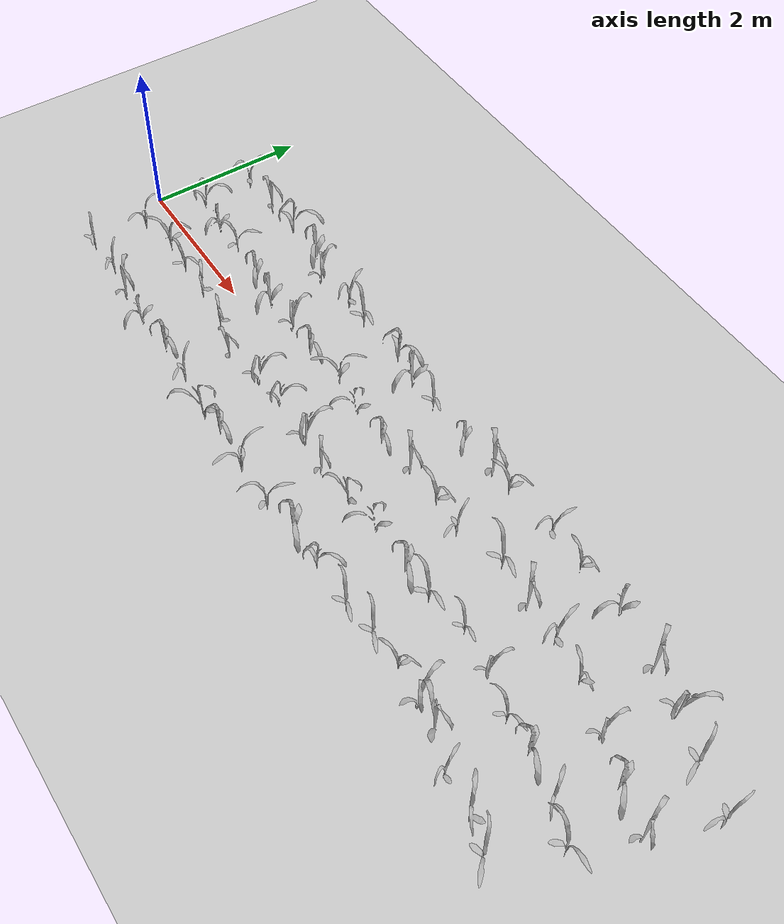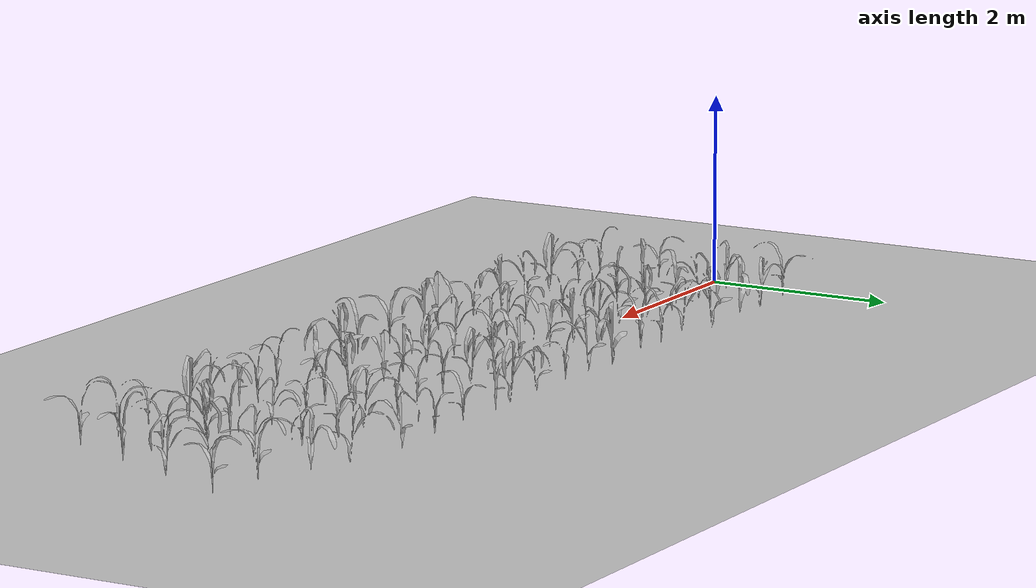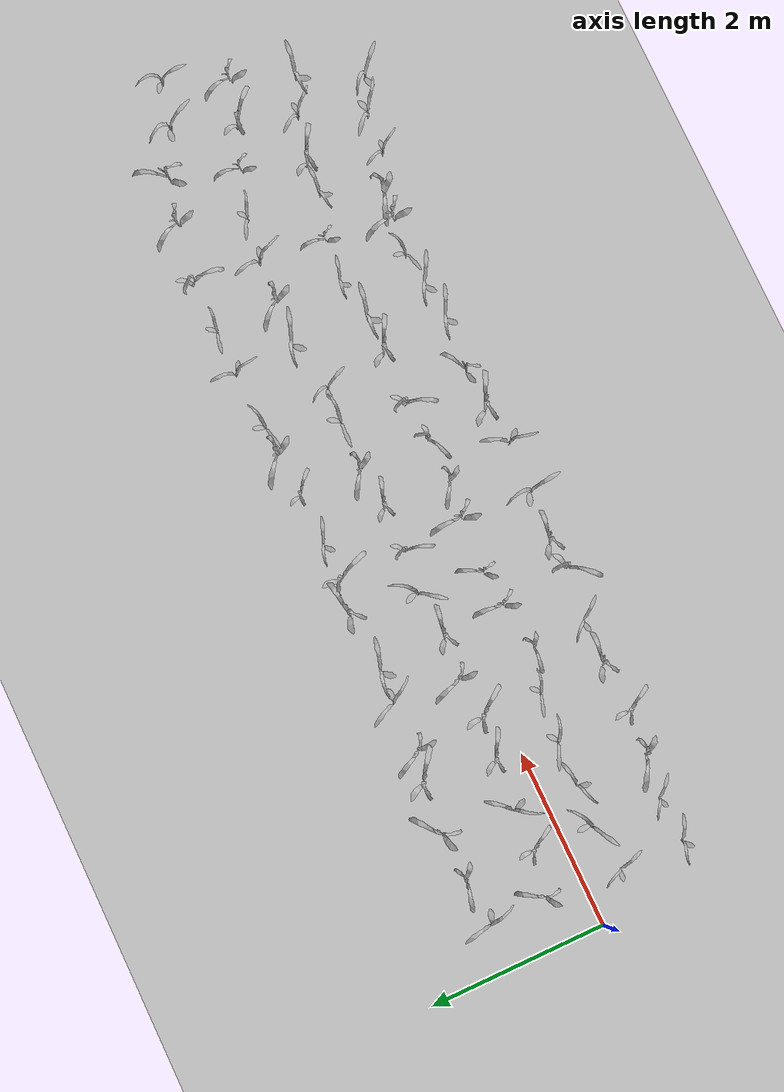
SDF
<sdf version="1.6">
 <world name="default">
  <light name="sun" type="directional">
   <pose>0 0 10 0 -0 0</pose>
   <diffuse>0.8 0.8 0.8 1</diffuse>
   <specular>0.2 0.2 0.2 1</specular>
   <attenuation>
    <range>1000</range>
    <constant>0.9</constant>
    <linear>0.01</linear>
    <quadratic>0.001</quadratic>
   </attenuation>
   <direction>-0.5 0.1 -0.9</direction>
  </light>
  <model name="ground_plane">
   <static>1</static>
   <link name="link">
    <collision name="collision">
     <geometry><plane><normal>0 0 1</normal><size>100 100</size></plane></geometry>
     <surface>
      <contact><collide_bitmask>65535</collide_bitmask></contact>
      <friction><ode><mu>100</mu><mu2>50</mu2></ode></friction>
     </surface>
    </collision>
    <visual name="visual">
     <cast_shadows>0</cast_shadows>
     <geometry><plane><normal>0 0 1</normal><size>100 100</size></plane></geometry>
     <material>
      <script><uri>file://media/materials/scripts/gazebo.material</uri><name>Gazebo/Grey</name></script>
     </material>
    </visual>
   </link>
  </model>
  <gravity>0 0 -9.8</gravity>
  <magnetic_field>6e-06 2.3e-05 -4.2e-05</magnetic_field>
  <atmosphere type="adiabatic"/>
  <physics name="default_physics" default="0" type="ode">
   <max_step_size>0.001</max_step_size>
   <real_time_factor>1</real_time_factor>
   <real_time_update_rate>1000</real_time_update_rate>
  </physics>
  <scene><ambient>0.4 0.4 0.4 1</ambient><background>0.7 0.7 0.7 1</background><shadows>1</shadows></scene>
  <audio><device>default</device></audio>
  <spherical_coordinates>
   <surface_model>EARTH_WGS84</surface_model>
   <latitude_deg>0</latitude_deg>
   <longitude_deg>0</longitude_deg>
   <elevation>0</elevation>
   <heading_deg>0</heading_deg>
  </spherical_coordinates>
  <model name="maize_01_0000">
   <pose>0.523966762746438 0.4150326742908084 0.05 0 -0 1.8050301071794776</pose>
   <link name="maize_01_0000_link">
    <inertial>
     <mass>5.0</mass>
     <inertia>
      <ixx>0.0033416667</ixx>
      <ixy>0</ixy>
      <ixz>0</ixz>
      <iyy>0.0033416667</iyy>
      <iyz>0</iyz>
      <izz>0.000016666667</izz>
     </inertia>
     <pose>0 0 0.1 0 0 0</pose>
    </inertial>
    <collision name="collision">
     <pose>0 0 0.2 0 -0 0</pose>
     <geometry><box><size>0.02 0.02 0.4</size></box></geometry>
     <surface><friction><ode><mu>10</mu><mu2>10</mu2></ode></friction></surface>
    </collision>
    <visual name="visual">
     <geometry>
      <mesh>
       <uri>model://maize_01/meshes/maize_01.dae</uri>
       <scale>0.5822569920695913 0.5822569920695913 0.5822569920695913</scale>
      </mesh>
     </geometry>
    </visual>
   </link>
  </model>
  <model name="maize_02_0001">
   <pose>0.5248532753365917 1.0798717160746447 0.05 0 -0 3.9507558975377663</pose>
   <link name="maize_02_0001_link">
    <inertial>
     <mass>5.0</mass>
     <inertia>
      <ixx>0.0033416667</ixx>
      <ixy>0</ixy>
      <ixz>0</ixz>
      <iyy>0.0033416667</iyy>
      <iyz>0</iyz>
      <izz>0.000016666667</izz>
     </inertia>
     <pose>0 0 0.1 0 0 0</pose>
    </inertial>
    <collision name="collision">
     <pose>0 0 0.2 0 -0 0</pose>
     <geometry><box><size>0.02 0.02 0.4</size></box></geometry>
     <surface><friction><ode><mu>10</mu><mu2>10</mu2></ode></friction></surface>
    </collision>
    <visual name="visual">
     <geometry>
      <mesh>
       <uri>model://maize_02/meshes/maize_02.dae</uri>
       <scale>0.6298423139953372 0.6298423139953372 0.6298423139953372</scale>
      </mesh>
     </geometry>
    </visual>
   </link>
  </model>
  <model name="maize_02_0002">
   <pose>0.46515844750414903 -0.4189155606194654 0.05 0 -0 0.9365900454225843</pose>
   <link name="maize_02_0002_link">
    <inertial>
     <mass>5.0</mass>
     <inertia>
      <ixx>0.0033416667</ixx>
      <ixy>0</ixy>
      <ixz>0</ixz>
      <iyy>0.0033416667</iyy>
      <iyz>0</iyz>
      <izz>0.000016666667</izz>
     </inertia>
     <pose>0 0 0.1 0 0 0</pose>
    </inertial>
    <collision name="collision">
     <pose>0 0 0.2 0 -0 0</pose>
     <geometry><box><size>0.02 0.02 0.4</size></box></geometry>
     <surface><friction><ode><mu>10</mu><mu2>10</mu2></ode></friction></surface>
    </collision>
    <visual name="visual">
     <geometry>
      <mesh>
       <uri>model://maize_02/meshes/maize_02.dae</uri>
       <scale>0.5298663133267577 0.5298663133267577 0.5298663133267577</scale>
      </mesh>
     </geometry>
    </visual>
   </link>
  </model>
  <model name="maize_02_0003">
   <pose>0.4602447589462634 -1.132043322837041 0.05 0 -0 1.7978640900643768</pose>
   <link name="maize_02_0003_link">
    <inertial>
     <mass>5.0</mass>
     <inertia>
      <ixx>0.0033416667</ixx>
      <ixy>0</ixy>
      <ixz>0</ixz>
      <iyy>0.0033416667</iyy>
      <iyz>0</iyz>
      <izz>0.000016666667</izz>
     </inertia>
     <pose>0 0 0.1 0 0 0</pose>
    </inertial>
    <collision name="collision">
     <pose>0 0 0.2 0 -0 0</pose>
     <geometry><box><size>0.02 0.02 0.4</size></box></geometry>
     <surface><friction><ode><mu>10</mu><mu2>10</mu2></ode></friction></surface>
    </collision>
    <visual name="visual">
     <geometry>
      <mesh>
       <uri>model://maize_02/meshes/maize_02.dae</uri>
       <scale>0.5381608076337044 0.5381608076337044 0.5381608076337044</scale>
      </mesh>
     </geometry>
    </visual>
   </link>
  </model>
  <model name="maize_01_0004">
   <pose>1.0199203152615652 0.35299629401230775 0.05 0 -0 6.0382954465742475</pose>
   <link name="maize_01_0004_link">
    <inertial>
     <mass>5.0</mass>
     <inertia>
      <ixx>0.0033416667</ixx>
      <ixy>0</ixy>
      <ixz>0</ixz>
      <iyy>0.0033416667</iyy>
      <iyz>0</iyz>
      <izz>0.000016666667</izz>
     </inertia>
     <pose>0 0 0.1 0 0 0</pose>
    </inertial>
    <collision name="collision">
     <pose>0 0 0.2 0 -0 0</pose>
     <geometry><box><size>0.02 0.02 0.4</size></box></geometry>
     <surface><friction><ode><mu>10</mu><mu2>10</mu2></ode></friction></surface>
    </collision>
    <visual name="visual">
     <geometry>
      <mesh>
       <uri>model://maize_01/meshes/maize_01.dae</uri>
       <scale>0.5396540530929095 0.5396540530929095 0.5396540530929095</scale>
      </mesh>
     </geometry>
    </visual>
   </link>
  </model>
  <model name="maize_01_0005">
   <pose>1.0654910295923556 1.105222662462426 0.05 0 -0 3.696057205758997</pose>
   <link name="maize_01_0005_link">
    <inertial>
     <mass>5.0</mass>
     <inertia>
      <ixx>0.0033416667</ixx>
      <ixy>0</ixy>
      <ixz>0</ixz>
      <iyy>0.0033416667</iyy>
      <iyz>0</iyz>
      <izz>0.000016666667</izz>
     </inertia>
     <pose>0 0 0.1 0 0 0</pose>
    </inertial>
    <collision name="collision">
     <pose>0 0 0.2 0 -0 0</pose>
     <geometry><box><size>0.02 0.02 0.4</size></box></geometry>
     <surface><friction><ode><mu>10</mu><mu2>10</mu2></ode></friction></surface>
    </collision>
    <visual name="visual">
     <geometry>
      <mesh>
       <uri>model://maize_01/meshes/maize_01.dae</uri>
       <scale>0.5877867600977696 0.5877867600977696 0.5877867600977696</scale>
      </mesh>
     </geometry>
    </visual>
   </link>
  </model>
  <model name="maize_02_0006">
   <pose>0.9898213369435384 -0.32654735532423174 0.05 0 -0 5.819287457244414</pose>
   <link name="maize_02_0006_link">
    <inertial>
     <mass>5.0</mass>
     <inertia>
      <ixx>0.0033416667</ixx>
      <ixy>0</ixy>
      <ixz>0</ixz>
      <iyy>0.0033416667</iyy>
      <iyz>0</iyz>
      <izz>0.000016666667</izz>
     </inertia>
     <pose>0 0 0.1 0 0 0</pose>
    </inertial>
    <collision name="collision">
     <pose>0 0 0.2 0 -0 0</pose>
     <geometry><box><size>0.02 0.02 0.4</size></box></geometry>
     <surface><friction><ode><mu>10</mu><mu2>10</mu2></ode></friction></surface>
    </collision>
    <visual name="visual">
     <geometry>
      <mesh>
       <uri>model://maize_02/meshes/maize_02.dae</uri>
       <scale>0.6463608204224338 0.6463608204224338 0.6463608204224338</scale>
      </mesh>
     </geometry>
    </visual>
   </link>
  </model>
  <model name="maize_02_0007">
   <pose>0.961585045974226 -1.1105220143562582 0.05 0 -0 1.4668708817369676</pose>
   <link name="maize_02_0007_link">
    <inertial>
     <mass>5.0</mass>
     <inertia>
      <ixx>0.0033416667</ixx>
      <ixy>0</ixy>
      <ixz>0</ixz>
      <iyy>0.0033416667</iyy>
      <iyz>0</iyz>
      <izz>0.000016666667</izz>
     </inertia>
     <pose>0 0 0.1 0 0 0</pose>
    </inertial>
    <collision name="collision">
     <pose>0 0 0.2 0 -0 0</pose>
     <geometry><box><size>0.02 0.02 0.4</size></box></geometry>
     <surface><friction><ode><mu>10</mu><mu2>10</mu2></ode></friction></surface>
    </collision>
    <visual name="visual">
     <geometry>
      <mesh>
       <uri>model://maize_02/meshes/maize_02.dae</uri>
       <scale>0.5000459984883049 0.5000459984883049 0.5000459984883049</scale>
      </mesh>
     </geometry>
    </visual>
   </link>
  </model>
  <model name="maize_02_0008">
   <pose>1.503632227551504 0.349260133318818 0.05 0 -0 3.076100888778547</pose>
   <link name="maize_02_0008_link">
    <inertial>
     <mass>5.0</mass>
     <inertia>
      <ixx>0.0033416667</ixx>
      <ixy>0</ixy>
      <ixz>0</ixz>
      <iyy>0.0033416667</iyy>
      <iyz>0</iyz>
      <izz>0.000016666667</izz>
     </inertia>
     <pose>0 0 0.1 0 0 0</pose>
    </inertial>
    <collision name="collision">
     <pose>0 0 0.2 0 -0 0</pose>
     <geometry><box><size>0.02 0.02 0.4</size></box></geometry>
     <surface><friction><ode><mu>10</mu><mu2>10</mu2></ode></friction></surface>
    </collision>
    <visual name="visual">
     <geometry>
      <mesh>
       <uri>model://maize_02/meshes/maize_02.dae</uri>
       <scale>0.6283412082809666 0.6283412082809666 0.6283412082809666</scale>
      </mesh>
     </geometry>
    </visual>
   </link>
  </model>
  <model name="maize_01_0009">
   <pose>1.558977972683102 1.1187317562141557 0.05 0 -0 1.4716533760433117</pose>
   <link name="maize_01_0009_link">
    <inertial>
     <mass>5.0</mass>
     <inertia>
      <ixx>0.0033416667</ixx>
      <ixy>0</ixy>
      <ixz>0</ixz>
      <iyy>0.0033416667</iyy>
      <iyz>0</iyz>
      <izz>0.000016666667</izz>
     </inertia>
     <pose>0 0 0.1 0 0 0</pose>
    </inertial>
    <collision name="collision">
     <pose>0 0 0.2 0 -0 0</pose>
     <geometry><box><size>0.02 0.02 0.4</size></box></geometry>
     <surface><friction><ode><mu>10</mu><mu2>10</mu2></ode></friction></surface>
    </collision>
    <visual name="visual">
     <geometry>
      <mesh>
       <uri>model://maize_01/meshes/maize_01.dae</uri>
       <scale>0.6826799311454922 0.6826799311454922 0.6826799311454922</scale>
      </mesh>
     </geometry>
    </visual>
   </link>
  </model>
  <model name="maize_02_0010">
   <pose>1.4536848330133545 -0.37425566543067856 0.05 0 -0 2.422375687809505</pose>
   <link name="maize_02_0010_link">
    <inertial>
     <mass>5.0</mass>
     <inertia>
      <ixx>0.0033416667</ixx>
      <ixy>0</ixy>
      <ixz>0</ixz>
      <iyy>0.0033416667</iyy>
      <iyz>0</iyz>
      <izz>0.000016666667</izz>
     </inertia>
     <pose>0 0 0.1 0 0 0</pose>
    </inertial>
    <collision name="collision">
     <pose>0 0 0.2 0 -0 0</pose>
     <geometry><box><size>0.02 0.02 0.4</size></box></geometry>
     <surface><friction><ode><mu>10</mu><mu2>10</mu2></ode></friction></surface>
    </collision>
    <visual name="visual">
     <geometry>
      <mesh>
       <uri>model://maize_02/meshes/maize_02.dae</uri>
       <scale>0.5736782465919196 0.5736782465919196 0.5736782465919196</scale>
      </mesh>
     </geometry>
    </visual>
   </link>
  </model>
  <model name="maize_01_0011">
   <pose>1.4444675356432104 -1.179642887555723 0.05 0 -0 3.4122779563719514</pose>
   <link name="maize_01_0011_link">
    <inertial>
     <mass>5.0</mass>
     <inertia>
      <ixx>0.0033416667</ixx>
      <ixy>0</ixy>
      <ixz>0</ixz>
      <iyy>0.0033416667</iyy>
      <iyz>0</iyz>
      <izz>0.000016666667</izz>
     </inertia>
     <pose>0 0 0.1 0 0 0</pose>
    </inertial>
    <collision name="collision">
     <pose>0 0 0.2 0 -0 0</pose>
     <geometry><box><size>0.02 0.02 0.4</size></box></geometry>
     <surface><friction><ode><mu>10</mu><mu2>10</mu2></ode></friction></surface>
    </collision>
    <visual name="visual">
     <geometry>
      <mesh>
       <uri>model://maize_01/meshes/maize_01.dae</uri>
       <scale>0.6784095090481377 0.6784095090481377 0.6784095090481377</scale>
      </mesh>
     </geometry>
    </visual>
   </link>
  </model>
  <model name="maize_01_0012">
   <pose>2.040732868175381 0.3005195694070919 0.05 0 -0 0.2899796782961759</pose>
   <link name="maize_01_0012_link">
    <inertial>
     <mass>5.0</mass>
     <inertia>
      <ixx>0.0033416667</ixx>
      <ixy>0</ixy>
      <ixz>0</ixz>
      <iyy>0.0033416667</iyy>
      <iyz>0</iyz>
      <izz>0.000016666667</izz>
     </inertia>
     <pose>0 0 0.1 0 0 0</pose>
    </inertial>
    <collision name="collision">
     <pose>0 0 0.2 0 -0 0</pose>
     <geometry><box><size>0.02 0.02 0.4</size></box></geometry>
     <surface><friction><ode><mu>10</mu><mu2>10</mu2></ode></friction></surface>
    </collision>
    <visual name="visual">
     <geometry>
      <mesh>
       <uri>model://maize_01/meshes/maize_01.dae</uri>
       <scale>0.595256392992198 0.595256392992198 0.595256392992198</scale>
      </mesh>
     </geometry>
    </visual>
   </link>
  </model>
  <model name="maize_01_0013">
   <pose>2.1368719891017847 1.106180763564035 0.05 0 -0 0.16974797185114474</pose>
   <link name="maize_01_0013_link">
    <inertial>
     <mass>5.0</mass>
     <inertia>
      <ixx>0.0033416667</ixx>
      <ixy>0</ixy>
      <ixz>0</ixz>
      <iyy>0.0033416667</iyy>
      <iyz>0</iyz>
      <izz>0.000016666667</izz>
     </inertia>
     <pose>0 0 0.1 0 0 0</pose>
    </inertial>
    <collision name="collision">
     <pose>0 0 0.2 0 -0 0</pose>
     <geometry><box><size>0.02 0.02 0.4</size></box></geometry>
     <surface><friction><ode><mu>10</mu><mu2>10</mu2></ode></friction></surface>
    </collision>
    <visual name="visual">
     <geometry>
      <mesh>
       <uri>model://maize_01/meshes/maize_01.dae</uri>
       <scale>0.6979724031252235 0.6979724031252235 0.6979724031252235</scale>
      </mesh>
     </geometry>
    </visual>
   </link>
  </model>
  <model name="maize_02_0014">
   <pose>1.931780257444167 -0.3824474502754521 0.05 0 -0 4.886222668759558</pose>
   <link name="maize_02_0014_link">
    <inertial>
     <mass>5.0</mass>
     <inertia>
      <ixx>0.0033416667</ixx>
      <ixy>0</ixy>
      <ixz>0</ixz>
      <iyy>0.0033416667</iyy>
      <iyz>0</iyz>
      <izz>0.000016666667</izz>
     </inertia>
     <pose>0 0 0.1 0 0 0</pose>
    </inertial>
    <collision name="collision">
     <pose>0 0 0.2 0 -0 0</pose>
     <geometry><box><size>0.02 0.02 0.4</size></box></geometry>
     <surface><friction><ode><mu>10</mu><mu2>10</mu2></ode></friction></surface>
    </collision>
    <visual name="visual">
     <geometry>
      <mesh>
       <uri>model://maize_02/meshes/maize_02.dae</uri>
       <scale>0.575836024601679 0.575836024601679 0.575836024601679</scale>
      </mesh>
     </geometry>
    </visual>
   </link>
  </model>
  <model name="maize_01_0015">
   <pose>1.9133926375941699 -1.2037670079675775 0.05 0 -0 6.033506653099774</pose>
   <link name="maize_01_0015_link">
    <inertial>
     <mass>5.0</mass>
     <inertia>
      <ixx>0.0033416667</ixx>
      <ixy>0</ixy>
      <ixz>0</ixz>
      <iyy>0.0033416667</iyy>
      <iyz>0</iyz>
      <izz>0.000016666667</izz>
     </inertia>
     <pose>0 0 0.1 0 0 0</pose>
    </inertial>
    <collision name="collision">
     <pose>0 0 0.2 0 -0 0</pose>
     <geometry><box><size>0.02 0.02 0.4</size></box></geometry>
     <surface><friction><ode><mu>10</mu><mu2>10</mu2></ode></friction></surface>
    </collision>
    <visual name="visual">
     <geometry>
      <mesh>
       <uri>model://maize_01/meshes/maize_01.dae</uri>
       <scale>0.5581267760683764 0.5581267760683764 0.5581267760683764</scale>
      </mesh>
     </geometry>
    </visual>
   </link>
  </model>
  <model name="maize_01_0016">
   <pose>2.510246999128019 0.23787252884046153 0.05 0 -0 6.144129899424734</pose>
   <link name="maize_01_0016_link">
    <inertial>
     <mass>5.0</mass>
     <inertia>
      <ixx>0.0033416667</ixx>
      <ixy>0</ixy>
      <ixz>0</ixz>
      <iyy>0.0033416667</iyy>
      <iyz>0</iyz>
      <izz>0.000016666667</izz>
     </inertia>
     <pose>0 0 0.1 0 0 0</pose>
    </inertial>
    <collision name="collision">
     <pose>0 0 0.2 0 -0 0</pose>
     <geometry><box><size>0.02 0.02 0.4</size></box></geometry>
     <surface><friction><ode><mu>10</mu><mu2>10</mu2></ode></friction></surface>
    </collision>
    <visual name="visual">
     <geometry>
      <mesh>
       <uri>model://maize_01/meshes/maize_01.dae</uri>
       <scale>0.6562338403578362 0.6562338403578362 0.6562338403578362</scale>
      </mesh>
     </geometry>
    </visual>
   </link>
  </model>
  <model name="maize_01_0017">
   <pose>2.493166982556981 0.9630720818078856 0.05 0 -0 2.861048662569731</pose>
   <link name="maize_01_0017_link">
    <inertial>
     <mass>5.0</mass>
     <inertia>
      <ixx>0.0033416667</ixx>
      <ixy>0</ixy>
      <ixz>0</ixz>
      <iyy>0.0033416667</iyy>
      <iyz>0</iyz>
      <izz>0.000016666667</izz>
     </inertia>
     <pose>0 0 0.1 0 0 0</pose>
    </inertial>
    <collision name="collision">
     <pose>0 0 0.2 0 -0 0</pose>
     <geometry><box><size>0.02 0.02 0.4</size></box></geometry>
     <surface><friction><ode><mu>10</mu><mu2>10</mu2></ode></friction></surface>
    </collision>
    <visual name="visual">
     <geometry>
      <mesh>
       <uri>model://maize_01/meshes/maize_01.dae</uri>
       <scale>0.629477505941498 0.629477505941498 0.629477505941498</scale>
      </mesh>
     </geometry>
    </visual>
   </link>
  </model>
  <model name="maize_02_0018">
   <pose>2.4838026439865604 -0.44149562420554733 0.05 0 -0 4.993970586922383</pose>
   <link name="maize_02_0018_link">
    <inertial>
     <mass>5.0</mass>
     <inertia>
      <ixx>0.0033416667</ixx>
      <ixy>0</ixy>
      <ixz>0</ixz>
      <iyy>0.0033416667</iyy>
      <iyz>0</iyz>
      <izz>0.000016666667</izz>
     </inertia>
     <pose>0 0 0.1 0 0 0</pose>
    </inertial>
    <collision name="collision">
     <pose>0 0 0.2 0 -0 0</pose>
     <geometry><box><size>0.02 0.02 0.4</size></box></geometry>
     <surface><friction><ode><mu>10</mu><mu2>10</mu2></ode></friction></surface>
    </collision>
    <visual name="visual">
     <geometry>
      <mesh>
       <uri>model://maize_02/meshes/maize_02.dae</uri>
       <scale>0.5095507926992316 0.5095507926992316 0.5095507926992316</scale>
      </mesh>
     </geometry>
    </visual>
   </link>
  </model>
  <model name="maize_01_0019">
   <pose>2.4671652501393573 -1.1738254497009892 0.05 0 -0 0.7211971315318042</pose>
   <link name="maize_01_0019_link">
    <inertial>
     <mass>5.0</mass>
     <inertia>
      <ixx>0.0033416667</ixx>
      <ixy>0</ixy>
      <ixz>0</ixz>
      <iyy>0.0033416667</iyy>
      <iyz>0</iyz>
      <izz>0.000016666667</izz>
     </inertia>
     <pose>0 0 0.1 0 0 0</pose>
    </inertial>
    <collision name="collision">
     <pose>0 0 0.2 0 -0 0</pose>
     <geometry><box><size>0.02 0.02 0.4</size></box></geometry>
     <surface><friction><ode><mu>10</mu><mu2>10</mu2></ode></friction></surface>
    </collision>
    <visual name="visual">
     <geometry>
      <mesh>
       <uri>model://maize_01/meshes/maize_01.dae</uri>
       <scale>0.629807478542989 0.629807478542989 0.629807478542989</scale>
      </mesh>
     </geometry>
    </visual>
   </link>
  </model>
  <model name="maize_01_0020">
   <pose>2.9889529004716753 0.25801577047027513 0.05 0 -0 2.71639642661828</pose>
   <link name="maize_01_0020_link">
    <inertial>
     <mass>5.0</mass>
     <inertia>
      <ixx>0.0033416667</ixx>
      <ixy>0</ixy>
      <ixz>0</ixz>
      <iyy>0.0033416667</iyy>
      <iyz>0</iyz>
      <izz>0.000016666667</izz>
     </inertia>
     <pose>0 0 0.1 0 0 0</pose>
    </inertial>
    <collision name="collision">
     <pose>0 0 0.2 0 -0 0</pose>
     <geometry><box><size>0.02 0.02 0.4</size></box></geometry>
     <surface><friction><ode><mu>10</mu><mu2>10</mu2></ode></friction></surface>
    </collision>
    <visual name="visual">
     <geometry>
      <mesh>
       <uri>model://maize_01/meshes/maize_01.dae</uri>
       <scale>0.6221070844538605 0.6221070844538605 0.6221070844538605</scale>
      </mesh>
     </geometry>
    </visual>
   </link>
  </model>
  <model name="maize_02_0021">
   <pose>3.0520632059223862 1.0240751103559858 0.05 0 -0 4.261147328329564</pose>
   <link name="maize_02_0021_link">
    <inertial>
     <mass>5.0</mass>
     <inertia>
      <ixx>0.0033416667</ixx>
      <ixy>0</ixy>
      <ixz>0</ixz>
      <iyy>0.0033416667</iyy>
      <iyz>0</iyz>
      <izz>0.000016666667</izz>
     </inertia>
     <pose>0 0 0.1 0 0 0</pose>
    </inertial>
    <collision name="collision">
     <pose>0 0 0.2 0 -0 0</pose>
     <geometry><box><size>0.02 0.02 0.4</size></box></geometry>
     <surface><friction><ode><mu>10</mu><mu2>10</mu2></ode></friction></surface>
    </collision>
    <visual name="visual">
     <geometry>
      <mesh>
       <uri>model://maize_02/meshes/maize_02.dae</uri>
       <scale>0.6331911358099501 0.6331911358099501 0.6331911358099501</scale>
      </mesh>
     </geometry>
    </visual>
   </link>
  </model>
  <model name="maize_01_0022">
   <pose>2.97400271973419 -0.5918598628877113 0.05 0 -0 3.7910285614634462</pose>
   <link name="maize_01_0022_link">
    <inertial>
     <mass>5.0</mass>
     <inertia>
      <ixx>0.0033416667</ixx>
      <ixy>0</ixy>
      <ixz>0</ixz>
      <iyy>0.0033416667</iyy>
      <iyz>0</iyz>
      <izz>0.000016666667</izz>
     </inertia>
     <pose>0 0 0.1 0 0 0</pose>
    </inertial>
    <collision name="collision">
     <pose>0 0 0.2 0 -0 0</pose>
     <geometry><box><size>0.02 0.02 0.4</size></box></geometry>
     <surface><friction><ode><mu>10</mu><mu2>10</mu2></ode></friction></surface>
    </collision>
    <visual name="visual">
     <geometry>
      <mesh>
       <uri>model://maize_01/meshes/maize_01.dae</uri>
       <scale>0.5028517858773822 0.5028517858773822 0.5028517858773822</scale>
      </mesh>
     </geometry>
    </visual>
   </link>
  </model>
  <model name="maize_02_0023">
   <pose>2.994720311939697 -1.1945998067587797 0.05 0 -0 1.3100654780904493</pose>
   <link name="maize_02_0023_link">
    <inertial>
     <mass>5.0</mass>
     <inertia>
      <ixx>0.0033416667</ixx>
      <ixy>0</ixy>
      <ixz>0</ixz>
      <iyy>0.0033416667</iyy>
      <iyz>0</iyz>
      <izz>0.000016666667</izz>
     </inertia>
     <pose>0 0 0.1 0 0 0</pose>
    </inertial>
    <collision name="collision">
     <pose>0 0 0.2 0 -0 0</pose>
     <geometry><box><size>0.02 0.02 0.4</size></box></geometry>
     <surface><friction><ode><mu>10</mu><mu2>10</mu2></ode></friction></surface>
    </collision>
    <visual name="visual">
     <geometry>
      <mesh>
       <uri>model://maize_02/meshes/maize_02.dae</uri>
       <scale>0.5348060385841131 0.5348060385841131 0.5348060385841131</scale>
      </mesh>
     </geometry>
    </visual>
   </link>
  </model>
  <model name="maize_01_0024">
   <pose>3.443074180217835 0.2284497880585611 0.05 0 -0 0.639792568922252</pose>
   <link name="maize_01_0024_link">
    <inertial>
     <mass>5.0</mass>
     <inertia>
      <ixx>0.0033416667</ixx>
      <ixy>0</ixy>
      <ixz>0</ixz>
      <iyy>0.0033416667</iyy>
      <iyz>0</iyz>
      <izz>0.000016666667</izz>
     </inertia>
     <pose>0 0 0.1 0 0 0</pose>
    </inertial>
    <collision name="collision">
     <pose>0 0 0.2 0 -0 0</pose>
     <geometry><box><size>0.02 0.02 0.4</size></box></geometry>
     <surface><friction><ode><mu>10</mu><mu2>10</mu2></ode></friction></surface>
    </collision>
    <visual name="visual">
     <geometry>
      <mesh>
       <uri>model://maize_01/meshes/maize_01.dae</uri>
       <scale>0.6128064751184193 0.6128064751184193 0.6128064751184193</scale>
      </mesh>
     </geometry>
    </visual>
   </link>
  </model>
  <model name="maize_02_0025">
   <pose>3.423280574257146 0.992229800525366 0.05 0 -0 1.9450103717449692</pose>
   <link name="maize_02_0025_link">
    <inertial>
     <mass>5.0</mass>
     <inertia>
      <ixx>0.0033416667</ixx>
      <ixy>0</ixy>
      <ixz>0</ixz>
      <iyy>0.0033416667</iyy>
      <iyz>0</iyz>
      <izz>0.000016666667</izz>
     </inertia>
     <pose>0 0 0.1 0 0 0</pose>
    </inertial>
    <collision name="collision">
     <pose>0 0 0.2 0 -0 0</pose>
     <geometry><box><size>0.02 0.02 0.4</size></box></geometry>
     <surface><friction><ode><mu>10</mu><mu2>10</mu2></ode></friction></surface>
    </collision>
    <visual name="visual">
     <geometry>
      <mesh>
       <uri>model://maize_02/meshes/maize_02.dae</uri>
       <scale>0.665604324518885 0.665604324518885 0.665604324518885</scale>
      </mesh>
     </geometry>
    </visual>
   </link>
  </model>
  <model name="maize_01_0026">
   <pose>3.5062867528112833 -0.5004778221379712 0.05 0 -0 2.3216417221331356</pose>
   <link name="maize_01_0026_link">
    <inertial>
     <mass>5.0</mass>
     <inertia>
      <ixx>0.0033416667</ixx>
      <ixy>0</ixy>
      <ixz>0</ixz>
      <iyy>0.0033416667</iyy>
      <iyz>0</iyz>
      <izz>0.000016666667</izz>
     </inertia>
     <pose>0 0 0.1 0 0 0</pose>
    </inertial>
    <collision name="collision">
     <pose>0 0 0.2 0 -0 0</pose>
     <geometry><box><size>0.02 0.02 0.4</size></box></geometry>
     <surface><friction><ode><mu>10</mu><mu2>10</mu2></ode></friction></surface>
    </collision>
    <visual name="visual">
     <geometry>
      <mesh>
       <uri>model://maize_01/meshes/maize_01.dae</uri>
       <scale>0.6098890040684718 0.6098890040684718 0.6098890040684718</scale>
      </mesh>
     </geometry>
    </visual>
   </link>
  </model>
  <model name="maize_01_0027">
   <pose>3.5920836885190277 -1.2672288973604182 0.05 0 -0 4.774702933948235</pose>
   <link name="maize_01_0027_link">
    <inertial>
     <mass>5.0</mass>
     <inertia>
      <ixx>0.0033416667</ixx>
      <ixy>0</ixy>
      <ixz>0</ixz>
      <iyy>0.0033416667</iyy>
      <iyz>0</iyz>
      <izz>0.000016666667</izz>
     </inertia>
     <pose>0 0 0.1 0 0 0</pose>
    </inertial>
    <collision name="collision">
     <pose>0 0 0.2 0 -0 0</pose>
     <geometry><box><size>0.02 0.02 0.4</size></box></geometry>
     <surface><friction><ode><mu>10</mu><mu2>10</mu2></ode></friction></surface>
    </collision>
    <visual name="visual">
     <geometry>
      <mesh>
       <uri>model://maize_01/meshes/maize_01.dae</uri>
       <scale>0.6556921403700694 0.6556921403700694 0.6556921403700694</scale>
      </mesh>
     </geometry>
    </visual>
   </link>
  </model>
  <model name="maize_02_0028">
   <pose>4.002339001380929 0.28708051347078645 0.05 0 -0 6.212871286915344</pose>
   <link name="maize_02_0028_link">
    <inertial>
     <mass>5.0</mass>
     <inertia>
      <ixx>0.0033416667</ixx>
      <ixy>0</ixy>
      <ixz>0</ixz>
      <iyy>0.0033416667</iyy>
      <iyz>0</iyz>
      <izz>0.000016666667</izz>
     </inertia>
     <pose>0 0 0.1 0 0 0</pose>
    </inertial>
    <collision name="collision">
     <pose>0 0 0.2 0 -0 0</pose>
     <geometry><box><size>0.02 0.02 0.4</size></box></geometry>
     <surface><friction><ode><mu>10</mu><mu2>10</mu2></ode></friction></surface>
    </collision>
    <visual name="visual">
     <geometry>
      <mesh>
       <uri>model://maize_02/meshes/maize_02.dae</uri>
       <scale>0.6356348580165118 0.6356348580165118 0.6356348580165118</scale>
      </mesh>
     </geometry>
    </visual>
   </link>
  </model>
  <model name="maize_01_0029">
   <pose>4.089465292540867 1.0392879885186976 0.05 0 -0 0.9478603963230247</pose>
   <link name="maize_01_0029_link">
    <inertial>
     <mass>5.0</mass>
     <inertia>
      <ixx>0.0033416667</ixx>
      <ixy>0</ixy>
      <ixz>0</ixz>
      <iyy>0.0033416667</iyy>
      <iyz>0</iyz>
      <izz>0.000016666667</izz>
     </inertia>
     <pose>0 0 0.1 0 0 0</pose>
    </inertial>
    <collision name="collision">
     <pose>0 0 0.2 0 -0 0</pose>
     <geometry><box><size>0.02 0.02 0.4</size></box></geometry>
     <surface><friction><ode><mu>10</mu><mu2>10</mu2></ode></friction></surface>
    </collision>
    <visual name="visual">
     <geometry>
      <mesh>
       <uri>model://maize_01/meshes/maize_01.dae</uri>
       <scale>0.6862345623201176 0.6862345623201176 0.6862345623201176</scale>
      </mesh>
     </geometry>
    </visual>
   </link>
  </model>
  <model name="maize_01_0030">
   <pose>3.9111913381568097 -0.46276025048916475 0.05 0 -0 1.9455105480501291</pose>
   <link name="maize_01_0030_link">
    <inertial>
     <mass>5.0</mass>
     <inertia>
      <ixx>0.0033416667</ixx>
      <ixy>0</ixy>
      <ixz>0</ixz>
      <iyy>0.0033416667</iyy>
      <iyz>0</iyz>
      <izz>0.000016666667</izz>
     </inertia>
     <pose>0 0 0.1 0 0 0</pose>
    </inertial>
    <collision name="collision">
     <pose>0 0 0.2 0 -0 0</pose>
     <geometry><box><size>0.02 0.02 0.4</size></box></geometry>
     <surface><friction><ode><mu>10</mu><mu2>10</mu2></ode></friction></surface>
    </collision>
    <visual name="visual">
     <geometry>
      <mesh>
       <uri>model://maize_01/meshes/maize_01.dae</uri>
       <scale>0.526570501130631 0.526570501130631 0.526570501130631</scale>
      </mesh>
     </geometry>
    </visual>
   </link>
  </model>
  <model name="maize_01_0031">
   <pose>3.8928818067296707 -1.2288936645430941 0.05 0 -0 0.6694644330116607</pose>
   <link name="maize_01_0031_link">
    <inertial>
     <mass>5.0</mass>
     <inertia>
      <ixx>0.0033416667</ixx>
      <ixy>0</ixy>
      <ixz>0</ixz>
      <iyy>0.0033416667</iyy>
      <iyz>0</iyz>
      <izz>0.000016666667</izz>
     </inertia>
     <pose>0 0 0.1 0 0 0</pose>
    </inertial>
    <collision name="collision">
     <pose>0 0 0.2 0 -0 0</pose>
     <geometry><box><size>0.02 0.02 0.4</size></box></geometry>
     <surface><friction><ode><mu>10</mu><mu2>10</mu2></ode></friction></surface>
    </collision>
    <visual name="visual">
     <geometry>
      <mesh>
       <uri>model://maize_01/meshes/maize_01.dae</uri>
       <scale>0.6072951427507317 0.6072951427507317 0.6072951427507317</scale>
      </mesh>
     </geometry>
    </visual>
   </link>
  </model>
  <model name="maize_01_0032">
   <pose>4.483130657835956 0.2181703435077315 0.05 0 -0 5.194716972884884</pose>
   <link name="maize_01_0032_link">
    <inertial>
     <mass>5.0</mass>
     <inertia>
      <ixx>0.0033416667</ixx>
      <ixy>0</ixy>
      <ixz>0</ixz>
      <iyy>0.0033416667</iyy>
      <iyz>0</iyz>
      <izz>0.000016666667</izz>
     </inertia>
     <pose>0 0 0.1 0 0 0</pose>
    </inertial>
    <collision name="collision">
     <pose>0 0 0.2 0 -0 0</pose>
     <geometry><box><size>0.02 0.02 0.4</size></box></geometry>
     <surface><friction><ode><mu>10</mu><mu2>10</mu2></ode></friction></surface>
    </collision>
    <visual name="visual">
     <geometry>
      <mesh>
       <uri>model://maize_01/meshes/maize_01.dae</uri>
       <scale>0.5381228093750381 0.5381228093750381 0.5381228093750381</scale>
      </mesh>
     </geometry>
    </visual>
   </link>
  </model>
  <model name="maize_01_0033">
   <pose>4.474949129762452 0.9862563068267514 0.05 0 -0 5.887725121790559</pose>
   <link name="maize_01_0033_link">
    <inertial>
     <mass>5.0</mass>
     <inertia>
      <ixx>0.0033416667</ixx>
      <ixy>0</ixy>
      <ixz>0</ixz>
      <iyy>0.0033416667</iyy>
      <iyz>0</iyz>
      <izz>0.000016666667</izz>
     </inertia>
     <pose>0 0 0.1 0 0 0</pose>
    </inertial>
    <collision name="collision">
     <pose>0 0 0.2 0 -0 0</pose>
     <geometry><box><size>0.02 0.02 0.4</size></box></geometry>
     <surface><friction><ode><mu>10</mu><mu2>10</mu2></ode></friction></surface>
    </collision>
    <visual name="visual">
     <geometry>
      <mesh>
       <uri>model://maize_01/meshes/maize_01.dae</uri>
       <scale>0.6739857275312071 0.6739857275312071 0.6739857275312071</scale>
      </mesh>
     </geometry>
    </visual>
   </link>
  </model>
  <model name="maize_01_0034">
   <pose>4.544771440879142 -0.5000676885154269 0.05 0 -0 2.4597328034436954</pose>
   <link name="maize_01_0034_link">
    <inertial>
     <mass>5.0</mass>
     <inertia>
      <ixx>0.0033416667</ixx>
      <ixy>0</ixy>
      <ixz>0</ixz>
      <iyy>0.0033416667</iyy>
      <iyz>0</iyz>
      <izz>0.000016666667</izz>
     </inertia>
     <pose>0 0 0.1 0 0 0</pose>
    </inertial>
    <collision name="collision">
     <pose>0 0 0.2 0 -0 0</pose>
     <geometry><box><size>0.02 0.02 0.4</size></box></geometry>
     <surface><friction><ode><mu>10</mu><mu2>10</mu2></ode></friction></surface>
    </collision>
    <visual name="visual">
     <geometry>
      <mesh>
       <uri>model://maize_01/meshes/maize_01.dae</uri>
       <scale>0.6755858032378665 0.6755858032378665 0.6755858032378665</scale>
      </mesh>
     </geometry>
    </visual>
   </link>
  </model>
  <model name="maize_02_0035">
   <pose>4.48810724896792 -1.282390259113714 0.05 0 -0 0.7057874232195723</pose>
   <link name="maize_02_0035_link">
    <inertial>
     <mass>5.0</mass>
     <inertia>
      <ixx>0.0033416667</ixx>
      <ixy>0</ixy>
      <ixz>0</ixz>
      <iyy>0.0033416667</iyy>
      <iyz>0</iyz>
      <izz>0.000016666667</izz>
     </inertia>
     <pose>0 0 0.1 0 0 0</pose>
    </inertial>
    <collision name="collision">
     <pose>0 0 0.2 0 -0 0</pose>
     <geometry><box><size>0.02 0.02 0.4</size></box></geometry>
     <surface><friction><ode><mu>10</mu><mu2>10</mu2></ode></friction></surface>
    </collision>
    <visual name="visual">
     <geometry>
      <mesh>
       <uri>model://maize_02/meshes/maize_02.dae</uri>
       <scale>0.6703926624739526 0.6703926624739526 0.6703926624739526</scale>
      </mesh>
     </geometry>
    </visual>
   </link>
  </model>
  <model name="maize_01_0036">
   <pose>4.991810056498151 0.2211237160717848 0.05 0 -0 0.48154976762973434</pose>
   <link name="maize_01_0036_link">
    <inertial>
     <mass>5.0</mass>
     <inertia>
      <ixx>0.0033416667</ixx>
      <ixy>0</ixy>
      <ixz>0</ixz>
      <iyy>0.0033416667</iyy>
      <iyz>0</iyz>
      <izz>0.000016666667</izz>
     </inertia>
     <pose>0 0 0.1 0 0 0</pose>
    </inertial>
    <collision name="collision">
     <pose>0 0 0.2 0 -0 0</pose>
     <geometry><box><size>0.02 0.02 0.4</size></box></geometry>
     <surface><friction><ode><mu>10</mu><mu2>10</mu2></ode></friction></surface>
    </collision>
    <visual name="visual">
     <geometry>
      <mesh>
       <uri>model://maize_01/meshes/maize_01.dae</uri>
       <scale>0.5598796415592937 0.5598796415592937 0.5598796415592937</scale>
      </mesh>
     </geometry>
    </visual>
   </link>
  </model>
  <model name="maize_02_0037">
   <pose>4.908736499374385 0.9768782011245747 0.05 0 -0 1.8294438370918091</pose>
   <link name="maize_02_0037_link">
    <inertial>
     <mass>5.0</mass>
     <inertia>
      <ixx>0.0033416667</ixx>
      <ixy>0</ixy>
      <ixz>0</ixz>
      <iyy>0.0033416667</iyy>
      <iyz>0</iyz>
      <izz>0.000016666667</izz>
     </inertia>
     <pose>0 0 0.1 0 0 0</pose>
    </inertial>
    <collision name="collision">
     <pose>0 0 0.2 0 -0 0</pose>
     <geometry><box><size>0.02 0.02 0.4</size></box></geometry>
     <surface><friction><ode><mu>10</mu><mu2>10</mu2></ode></friction></surface>
    </collision>
    <visual name="visual">
     <geometry>
      <mesh>
       <uri>model://maize_02/meshes/maize_02.dae</uri>
       <scale>0.5496664147344748 0.5496664147344748 0.5496664147344748</scale>
      </mesh>
     </geometry>
    </visual>
   </link>
  </model>
  <model name="maize_01_0038">
   <pose>4.976571551156914 -0.5525297962804545 0.05 0 -0 3.379482973106335</pose>
   <link name="maize_01_0038_link">
    <inertial>
     <mass>5.0</mass>
     <inertia>
      <ixx>0.0033416667</ixx>
      <ixy>0</ixy>
      <ixz>0</ixz>
      <iyy>0.0033416667</iyy>
      <iyz>0</iyz>
      <izz>0.000016666667</izz>
     </inertia>
     <pose>0 0 0.1 0 0 0</pose>
    </inertial>
    <collision name="collision">
     <pose>0 0 0.2 0 -0 0</pose>
     <geometry><box><size>0.02 0.02 0.4</size></box></geometry>
     <surface><friction><ode><mu>10</mu><mu2>10</mu2></ode></friction></surface>
    </collision>
    <visual name="visual">
     <geometry>
      <mesh>
       <uri>model://maize_01/meshes/maize_01.dae</uri>
       <scale>0.5454395372070664 0.5454395372070664 0.5454395372070664</scale>
      </mesh>
     </geometry>
    </visual>
   </link>
  </model>
  <model name="maize_02_0039">
   <pose>5.072777903811759 -1.2960011632742425 0.05 0 -0 3.4086793151289485</pose>
   <link name="maize_02_0039_link">
    <inertial>
     <mass>5.0</mass>
     <inertia>
      <ixx>0.0033416667</ixx>
      <ixy>0</ixy>
      <ixz>0</ixz>
      <iyy>0.0033416667</iyy>
      <iyz>0</iyz>
      <izz>0.000016666667</izz>
     </inertia>
     <pose>0 0 0.1 0 0 0</pose>
    </inertial>
    <collision name="collision">
     <pose>0 0 0.2 0 -0 0</pose>
     <geometry><box><size>0.02 0.02 0.4</size></box></geometry>
     <surface><friction><ode><mu>10</mu><mu2>10</mu2></ode></friction></surface>
    </collision>
    <visual name="visual">
     <geometry>
      <mesh>
       <uri>model://maize_02/meshes/maize_02.dae</uri>
       <scale>0.6224902555846658 0.6224902555846658 0.6224902555846658</scale>
      </mesh>
     </geometry>
    </visual>
   </link>
  </model>
  <model name="maize_01_0040">
   <pose>5.506786994470189 0.2656293258427953 0.05 0 -0 3.3924186708575643</pose>
   <link name="maize_01_0040_link">
    <inertial>
     <mass>5.0</mass>
     <inertia>
      <ixx>0.0033416667</ixx>
      <ixy>0</ixy>
      <ixz>0</ixz>
      <iyy>0.0033416667</iyy>
      <iyz>0</iyz>
      <izz>0.000016666667</izz>
     </inertia>
     <pose>0 0 0.1 0 0 0</pose>
    </inertial>
    <collision name="collision">
     <pose>0 0 0.2 0 -0 0</pose>
     <geometry><box><size>0.02 0.02 0.4</size></box></geometry>
     <surface><friction><ode><mu>10</mu><mu2>10</mu2></ode></friction></surface>
    </collision>
    <visual name="visual">
     <geometry>
      <mesh>
       <uri>model://maize_01/meshes/maize_01.dae</uri>
       <scale>0.6189998295043194 0.6189998295043194 0.6189998295043194</scale>
      </mesh>
     </geometry>
    </visual>
   </link>
  </model>
  <model name="maize_01_0041">
   <pose>5.498270994802505 0.9851649610068504 0.05 0 -0 0.06025964583949141</pose>
   <link name="maize_01_0041_link">
    <inertial>
     <mass>5.0</mass>
     <inertia>
      <ixx>0.0033416667</ixx>
      <ixy>0</ixy>
      <ixz>0</ixz>
      <iyy>0.0033416667</iyy>
      <iyz>0</iyz>
      <izz>0.000016666667</izz>
     </inertia>
     <pose>0 0 0.1 0 0 0</pose>
    </inertial>
    <collision name="collision">
     <pose>0 0 0.2 0 -0 0</pose>
     <geometry><box><size>0.02 0.02 0.4</size></box></geometry>
     <surface><friction><ode><mu>10</mu><mu2>10</mu2></ode></friction></surface>
    </collision>
    <visual name="visual">
     <geometry>
      <mesh>
       <uri>model://maize_01/meshes/maize_01.dae</uri>
       <scale>0.5000915318955779 0.5000915318955779 0.5000915318955779</scale>
      </mesh>
     </geometry>
    </visual>
   </link>
  </model>
  <model name="maize_01_0042">
   <pose>5.479430346156631 -0.5195344718169158 0.05 0 -0 4.317994222408603</pose>
   <link name="maize_01_0042_link">
    <inertial>
     <mass>5.0</mass>
     <inertia>
      <ixx>0.0033416667</ixx>
      <ixy>0</ixy>
      <ixz>0</ixz>
      <iyy>0.0033416667</iyy>
      <iyz>0</iyz>
      <izz>0.000016666667</izz>
     </inertia>
     <pose>0 0 0.1 0 0 0</pose>
    </inertial>
    <collision name="collision">
     <pose>0 0 0.2 0 -0 0</pose>
     <geometry><box><size>0.02 0.02 0.4</size></box></geometry>
     <surface><friction><ode><mu>10</mu><mu2>10</mu2></ode></friction></surface>
    </collision>
    <visual name="visual">
     <geometry>
      <mesh>
       <uri>model://maize_01/meshes/maize_01.dae</uri>
       <scale>0.5534661989044314 0.5534661989044314 0.5534661989044314</scale>
      </mesh>
     </geometry>
    </visual>
   </link>
  </model>
  <model name="maize_01_0043">
   <pose>5.494622844473126 -1.2155527549326124 0.05 0 -0 0.37965837072912256</pose>
   <link name="maize_01_0043_link">
    <inertial>
     <mass>5.0</mass>
     <inertia>
      <ixx>0.0033416667</ixx>
      <ixy>0</ixy>
      <ixz>0</ixz>
      <iyy>0.0033416667</iyy>
      <iyz>0</iyz>
      <izz>0.000016666667</izz>
     </inertia>
     <pose>0 0 0.1 0 0 0</pose>
    </inertial>
    <collision name="collision">
     <pose>0 0 0.2 0 -0 0</pose>
     <geometry><box><size>0.02 0.02 0.4</size></box></geometry>
     <surface><friction><ode><mu>10</mu><mu2>10</mu2></ode></friction></surface>
    </collision>
    <visual name="visual">
     <geometry>
      <mesh>
       <uri>model://maize_01/meshes/maize_01.dae</uri>
       <scale>0.6962699826558162 0.6962699826558162 0.6962699826558162</scale>
      </mesh>
     </geometry>
    </visual>
   </link>
  </model>
  <model name="maize_02_0044">
   <pose>6.02254541849747 0.2537100269036799 0.05 0 -0 5.268390102434163</pose>
   <link name="maize_02_0044_link">
    <inertial>
     <mass>5.0</mass>
     <inertia>
      <ixx>0.0033416667</ixx>
      <ixy>0</ixy>
      <ixz>0</ixz>
      <iyy>0.0033416667</iyy>
      <iyz>0</iyz>
      <izz>0.000016666667</izz>
     </inertia>
     <pose>0 0 0.1 0 0 0</pose>
    </inertial>
    <collision name="collision">
     <pose>0 0 0.2 0 -0 0</pose>
     <geometry><box><size>0.02 0.02 0.4</size></box></geometry>
     <surface><friction><ode><mu>10</mu><mu2>10</mu2></ode></friction></surface>
    </collision>
    <visual name="visual">
     <geometry>
      <mesh>
       <uri>model://maize_02/meshes/maize_02.dae</uri>
       <scale>0.6088828733099652 0.6088828733099652 0.6088828733099652</scale>
      </mesh>
     </geometry>
    </visual>
   </link>
  </model>
  <model name="maize_01_0045">
   <pose>6.021867439145475 1.0064633467937198 0.05 0 -0 3.332251710796354</pose>
   <link name="maize_01_0045_link">
    <inertial>
     <mass>5.0</mass>
     <inertia>
      <ixx>0.0033416667</ixx>
      <ixy>0</ixy>
      <ixz>0</ixz>
      <iyy>0.0033416667</iyy>
      <iyz>0</iyz>
      <izz>0.000016666667</izz>
     </inertia>
     <pose>0 0 0.1 0 0 0</pose>
    </inertial>
    <collision name="collision">
     <pose>0 0 0.2 0 -0 0</pose>
     <geometry><box><size>0.02 0.02 0.4</size></box></geometry>
     <surface><friction><ode><mu>10</mu><mu2>10</mu2></ode></friction></surface>
    </collision>
    <visual name="visual">
     <geometry>
      <mesh>
       <uri>model://maize_01/meshes/maize_01.dae</uri>
       <scale>0.6867273413716238 0.6867273413716238 0.6867273413716238</scale>
      </mesh>
     </geometry>
    </visual>
   </link>
  </model>
  <model name="maize_01_0046">
   <pose>5.932401994137389 -0.46470037149348664 0.05 0 -0 5.085144024606066</pose>
   <link name="maize_01_0046_link">
    <inertial>
     <mass>5.0</mass>
     <inertia>
      <ixx>0.0033416667</ixx>
      <ixy>0</ixy>
      <ixz>0</ixz>
      <iyy>0.0033416667</iyy>
      <iyz>0</iyz>
      <izz>0.000016666667</izz>
     </inertia>
     <pose>0 0 0.1 0 0 0</pose>
    </inertial>
    <collision name="collision">
     <pose>0 0 0.2 0 -0 0</pose>
     <geometry><box><size>0.02 0.02 0.4</size></box></geometry>
     <surface><friction><ode><mu>10</mu><mu2>10</mu2></ode></friction></surface>
    </collision>
    <visual name="visual">
     <geometry>
      <mesh>
       <uri>model://maize_01/meshes/maize_01.dae</uri>
       <scale>0.5899681368352446 0.5899681368352446 0.5899681368352446</scale>
      </mesh>
     </geometry>
    </visual>
   </link>
  </model>
  <model name="maize_01_0047">
   <pose>5.974389578275147 -1.2238915524115812 0.05 0 -0 1.3758996563627348</pose>
   <link name="maize_01_0047_link">
    <inertial>
     <mass>5.0</mass>
     <inertia>
      <ixx>0.0033416667</ixx>
      <ixy>0</ixy>
      <ixz>0</ixz>
      <iyy>0.0033416667</iyy>
      <iyz>0</iyz>
      <izz>0.000016666667</izz>
     </inertia>
     <pose>0 0 0.1 0 0 0</pose>
    </inertial>
    <collision name="collision">
     <pose>0 0 0.2 0 -0 0</pose>
     <geometry><box><size>0.02 0.02 0.4</size></box></geometry>
     <surface><friction><ode><mu>10</mu><mu2>10</mu2></ode></friction></surface>
    </collision>
    <visual name="visual">
     <geometry>
      <mesh>
       <uri>model://maize_01/meshes/maize_01.dae</uri>
       <scale>0.5517075941704092 0.5517075941704092 0.5517075941704092</scale>
      </mesh>
     </geometry>
    </visual>
   </link>
  </model>
  <model name="maize_02_0048">
   <pose>6.444683934957754 0.21806997869283193 0.05 0 -0 1.0231611283328046</pose>
   <link name="maize_02_0048_link">
    <inertial>
     <mass>5.0</mass>
     <inertia>
      <ixx>0.0033416667</ixx>
      <ixy>0</ixy>
      <ixz>0</ixz>
      <iyy>0.0033416667</iyy>
      <iyz>0</iyz>
      <izz>0.000016666667</izz>
     </inertia>
     <pose>0 0 0.1 0 0 0</pose>
    </inertial>
    <collision name="collision">
     <pose>0 0 0.2 0 -0 0</pose>
     <geometry><box><size>0.02 0.02 0.4</size></box></geometry>
     <surface><friction><ode><mu>10</mu><mu2>10</mu2></ode></friction></surface>
    </collision>
    <visual name="visual">
     <geometry>
      <mesh>
       <uri>model://maize_02/meshes/maize_02.dae</uri>
       <scale>0.5222971193343772 0.5222971193343772 0.5222971193343772</scale>
      </mesh>
     </geometry>
    </visual>
   </link>
  </model>
  <model name="maize_02_0049">
   <pose>6.311951254254064 1.011576644294995 0.05 0 -0 5.504198045658767</pose>
   <link name="maize_02_0049_link">
    <inertial>
     <mass>5.0</mass>
     <inertia>
      <ixx>0.0033416667</ixx>
      <ixy>0</ixy>
      <ixz>0</ixz>
      <iyy>0.0033416667</iyy>
      <iyz>0</iyz>
      <izz>0.000016666667</izz>
     </inertia>
     <pose>0 0 0.1 0 0 0</pose>
    </inertial>
    <collision name="collision">
     <pose>0 0 0.2 0 -0 0</pose>
     <geometry><box><size>0.02 0.02 0.4</size></box></geometry>
     <surface><friction><ode><mu>10</mu><mu2>10</mu2></ode></friction></surface>
    </collision>
    <visual name="visual">
     <geometry>
      <mesh>
       <uri>model://maize_02/meshes/maize_02.dae</uri>
       <scale>0.5701051856462379 0.5701051856462379 0.5701051856462379</scale>
      </mesh>
     </geometry>
    </visual>
   </link>
  </model>
  <model name="maize_01_0050">
   <pose>6.53616275845879 -0.49190842154945386 0.05 0 -0 0.33308074377836916</pose>
   <link name="maize_01_0050_link">
    <inertial>
     <mass>5.0</mass>
     <inertia>
      <ixx>0.0033416667</ixx>
      <ixy>0</ixy>
      <ixz>0</ixz>
      <iyy>0.0033416667</iyy>
      <iyz>0</iyz>
      <izz>0.000016666667</izz>
     </inertia>
     <pose>0 0 0.1 0 0 0</pose>
    </inertial>
    <collision name="collision">
     <pose>0 0 0.2 0 -0 0</pose>
     <geometry><box><size>0.02 0.02 0.4</size></box></geometry>
     <surface><friction><ode><mu>10</mu><mu2>10</mu2></ode></friction></surface>
    </collision>
    <visual name="visual">
     <geometry>
      <mesh>
       <uri>model://maize_01/meshes/maize_01.dae</uri>
       <scale>0.6685947104741558 0.6685947104741558 0.6685947104741558</scale>
      </mesh>
     </geometry>
    </visual>
   </link>
  </model>
  <model name="maize_02_0051">
   <pose>6.611361487242681 -1.2605063685053592 0.05 0 -0 1.7884036289483325</pose>
   <link name="maize_02_0051_link">
    <inertial>
     <mass>5.0</mass>
     <inertia>
      <ixx>0.0033416667</ixx>
      <ixy>0</ixy>
      <ixz>0</ixz>
      <iyy>0.0033416667</iyy>
      <iyz>0</iyz>
      <izz>0.000016666667</izz>
     </inertia>
     <pose>0 0 0.1 0 0 0</pose>
    </inertial>
    <collision name="collision">
     <pose>0 0 0.2 0 -0 0</pose>
     <geometry><box><size>0.02 0.02 0.4</size></box></geometry>
     <surface><friction><ode><mu>10</mu><mu2>10</mu2></ode></friction></surface>
    </collision>
    <visual name="visual">
     <geometry>
      <mesh>
       <uri>model://maize_02/meshes/maize_02.dae</uri>
       <scale>0.6225692680401886 0.6225692680401886 0.6225692680401886</scale>
      </mesh>
     </geometry>
    </visual>
   </link>
  </model>
  <model name="maize_02_0052">
   <pose>7.047655717057351 0.3668921904029307 0.05 0 -0 1.865239226065937</pose>
   <link name="maize_02_0052_link">
    <inertial>
     <mass>5.0</mass>
     <inertia>
      <ixx>0.0033416667</ixx>
      <ixy>0</ixy>
      <ixz>0</ixz>
      <iyy>0.0033416667</iyy>
      <iyz>0</iyz>
      <izz>0.000016666667</izz>
     </inertia>
     <pose>0 0 0.1 0 0 0</pose>
    </inertial>
    <collision name="collision">
     <pose>0 0 0.2 0 -0 0</pose>
     <geometry><box><size>0.02 0.02 0.4</size></box></geometry>
     <surface><friction><ode><mu>10</mu><mu2>10</mu2></ode></friction></surface>
    </collision>
    <visual name="visual">
     <geometry>
      <mesh>
       <uri>model://maize_02/meshes/maize_02.dae</uri>
       <scale>0.6868021087822107 0.6868021087822107 0.6868021087822107</scale>
      </mesh>
     </geometry>
    </visual>
   </link>
  </model>
  <model name="maize_02_0053">
   <pose>7.002225742621037 1.0586696913169389 0.05 0 -0 3.749618994481808</pose>
   <link name="maize_02_0053_link">
    <inertial>
     <mass>5.0</mass>
     <inertia>
      <ixx>0.0033416667</ixx>
      <ixy>0</ixy>
      <ixz>0</ixz>
      <iyy>0.0033416667</iyy>
      <iyz>0</iyz>
      <izz>0.000016666667</izz>
     </inertia>
     <pose>0 0 0.1 0 0 0</pose>
    </inertial>
    <collision name="collision">
     <pose>0 0 0.2 0 -0 0</pose>
     <geometry><box><size>0.02 0.02 0.4</size></box></geometry>
     <surface><friction><ode><mu>10</mu><mu2>10</mu2></ode></friction></surface>
    </collision>
    <visual name="visual">
     <geometry>
      <mesh>
       <uri>model://maize_02/meshes/maize_02.dae</uri>
       <scale>0.5549107990418974 0.5549107990418974 0.5549107990418974</scale>
      </mesh>
     </geometry>
    </visual>
   </link>
  </model>
  <model name="maize_02_0054">
   <pose>6.964805699102833 -0.4964306345051091 0.05 0 -0 2.0242427335745856</pose>
   <link name="maize_02_0054_link">
    <inertial>
     <mass>5.0</mass>
     <inertia>
      <ixx>0.0033416667</ixx>
      <ixy>0</ixy>
      <ixz>0</ixz>
      <iyy>0.0033416667</iyy>
      <iyz>0</iyz>
      <izz>0.000016666667</izz>
     </inertia>
     <pose>0 0 0.1 0 0 0</pose>
    </inertial>
    <collision name="collision">
     <pose>0 0 0.2 0 -0 0</pose>
     <geometry><box><size>0.02 0.02 0.4</size></box></geometry>
     <surface><friction><ode><mu>10</mu><mu2>10</mu2></ode></friction></surface>
    </collision>
    <visual name="visual">
     <geometry>
      <mesh>
       <uri>model://maize_02/meshes/maize_02.dae</uri>
       <scale>0.6621043652803483 0.6621043652803483 0.6621043652803483</scale>
      </mesh>
     </geometry>
    </visual>
   </link>
  </model>
  <model name="maize_02_0055">
   <pose>7.040403497226146 -1.2146936146891378 0.05 0 -0 1.7073671391820333</pose>
   <link name="maize_02_0055_link">
    <inertial>
     <mass>5.0</mass>
     <inertia>
      <ixx>0.0033416667</ixx>
      <ixy>0</ixy>
      <ixz>0</ixz>
      <iyy>0.0033416667</iyy>
      <iyz>0</iyz>
      <izz>0.000016666667</izz>
     </inertia>
     <pose>0 0 0.1 0 0 0</pose>
    </inertial>
    <collision name="collision">
     <pose>0 0 0.2 0 -0 0</pose>
     <geometry><box><size>0.02 0.02 0.4</size></box></geometry>
     <surface><friction><ode><mu>10</mu><mu2>10</mu2></ode></friction></surface>
    </collision>
    <visual name="visual">
     <geometry>
      <mesh>
       <uri>model://maize_02/meshes/maize_02.dae</uri>
       <scale>0.6301210235145418 0.6301210235145418 0.6301210235145418</scale>
      </mesh>
     </geometry>
    </visual>
   </link>
  </model>
  <model name="maize_01_0056">
   <pose>7.564689000184168 0.31163713333273607 0.05 0 -0 3.188919088596986</pose>
   <link name="maize_01_0056_link">
    <inertial>
     <mass>5.0</mass>
     <inertia>
      <ixx>0.0033416667</ixx>
      <ixy>0</ixy>
      <ixz>0</ixz>
      <iyy>0.0033416667</iyy>
      <iyz>0</iyz>
      <izz>0.000016666667</izz>
     </inertia>
     <pose>0 0 0.1 0 0 0</pose>
    </inertial>
    <collision name="collision">
     <pose>0 0 0.2 0 -0 0</pose>
     <geometry><box><size>0.02 0.02 0.4</size></box></geometry>
     <surface><friction><ode><mu>10</mu><mu2>10</mu2></ode></friction></surface>
    </collision>
    <visual name="visual">
     <geometry>
      <mesh>
       <uri>model://maize_01/meshes/maize_01.dae</uri>
       <scale>0.6456038164937912 0.6456038164937912 0.6456038164937912</scale>
      </mesh>
     </geometry>
    </visual>
   </link>
  </model>
  <model name="maize_02_0057">
   <pose>7.500975361317406 1.0499312067313706 0.05 0 -0 5.141058910653974</pose>
   <link name="maize_02_0057_link">
    <inertial>
     <mass>5.0</mass>
     <inertia>
      <ixx>0.0033416667</ixx>
      <ixy>0</ixy>
      <ixz>0</ixz>
      <iyy>0.0033416667</iyy>
      <iyz>0</iyz>
      <izz>0.000016666667</izz>
     </inertia>
     <pose>0 0 0.1 0 0 0</pose>
    </inertial>
    <collision name="collision">
     <pose>0 0 0.2 0 -0 0</pose>
     <geometry><box><size>0.02 0.02 0.4</size></box></geometry>
     <surface><friction><ode><mu>10</mu><mu2>10</mu2></ode></friction></surface>
    </collision>
    <visual name="visual">
     <geometry>
      <mesh>
       <uri>model://maize_02/meshes/maize_02.dae</uri>
       <scale>0.5251215965367916 0.5251215965367916 0.5251215965367916</scale>
      </mesh>
     </geometry>
    </visual>
   </link>
  </model>
  <model name="maize_02_0058">
   <pose>7.455712312881643 -0.3977243474003614 0.05 0 -0 1.9446974029243165</pose>
   <link name="maize_02_0058_link">
    <inertial>
     <mass>5.0</mass>
     <inertia>
      <ixx>0.0033416667</ixx>
      <ixy>0</ixy>
      <ixz>0</ixz>
      <iyy>0.0033416667</iyy>
      <iyz>0</iyz>
      <izz>0.000016666667</izz>
     </inertia>
     <pose>0 0 0.1 0 0 0</pose>
    </inertial>
    <collision name="collision">
     <pose>0 0 0.2 0 -0 0</pose>
     <geometry><box><size>0.02 0.02 0.4</size></box></geometry>
     <surface><friction><ode><mu>10</mu><mu2>10</mu2></ode></friction></surface>
    </collision>
    <visual name="visual">
     <geometry>
      <mesh>
       <uri>model://maize_02/meshes/maize_02.dae</uri>
       <scale>0.5105369562286869 0.5105369562286869 0.5105369562286869</scale>
      </mesh>
     </geometry>
    </visual>
   </link>
  </model>
  <model name="maize_02_0059">
   <pose>7.426569444041071 -1.168700941892246 0.05 0 -0 5.573964091727801</pose>
   <link name="maize_02_0059_link">
    <inertial>
     <mass>5.0</mass>
     <inertia>
      <ixx>0.0033416667</ixx>
      <ixy>0</ixy>
      <ixz>0</ixz>
      <iyy>0.0033416667</iyy>
      <iyz>0</iyz>
      <izz>0.000016666667</izz>
     </inertia>
     <pose>0 0 0.1 0 0 0</pose>
    </inertial>
    <collision name="collision">
     <pose>0 0 0.2 0 -0 0</pose>
     <geometry><box><size>0.02 0.02 0.4</size></box></geometry>
     <surface><friction><ode><mu>10</mu><mu2>10</mu2></ode></friction></surface>
    </collision>
    <visual name="visual">
     <geometry>
      <mesh>
       <uri>model://maize_02/meshes/maize_02.dae</uri>
       <scale>0.5241416613408271 0.5241416613408271 0.5241416613408271</scale>
      </mesh>
     </geometry>
    </visual>
   </link>
  </model>
  <model name="maize_02_0060">
   <pose>8.024216891501732 0.3117248870357677 0.05 0 -0 4.009393099995125</pose>
   <link name="maize_02_0060_link">
    <inertial>
     <mass>5.0</mass>
     <inertia>
      <ixx>0.0033416667</ixx>
      <ixy>0</ixy>
      <ixz>0</ixz>
      <iyy>0.0033416667</iyy>
      <iyz>0</iyz>
      <izz>0.000016666667</izz>
     </inertia>
     <pose>0 0 0.1 0 0 0</pose>
    </inertial>
    <collision name="collision">
     <pose>0 0 0.2 0 -0 0</pose>
     <geometry><box><size>0.02 0.02 0.4</size></box></geometry>
     <surface><friction><ode><mu>10</mu><mu2>10</mu2></ode></friction></surface>
    </collision>
    <visual name="visual">
     <geometry>
      <mesh>
       <uri>model://maize_02/meshes/maize_02.dae</uri>
       <scale>0.619068009571125 0.619068009571125 0.619068009571125</scale>
      </mesh>
     </geometry>
    </visual>
   </link>
  </model>
  <model name="maize_01_0061">
   <pose>8.114442692044541 1.066516804768334 0.05 0 -0 5.434871950774438</pose>
   <link name="maize_01_0061_link">
    <inertial>
     <mass>5.0</mass>
     <inertia>
      <ixx>0.0033416667</ixx>
      <ixy>0</ixy>
      <ixz>0</ixz>
      <iyy>0.0033416667</iyy>
      <iyz>0</iyz>
      <izz>0.000016666667</izz>
     </inertia>
     <pose>0 0 0.1 0 0 0</pose>
    </inertial>
    <collision name="collision">
     <pose>0 0 0.2 0 -0 0</pose>
     <geometry><box><size>0.02 0.02 0.4</size></box></geometry>
     <surface><friction><ode><mu>10</mu><mu2>10</mu2></ode></friction></surface>
    </collision>
    <visual name="visual">
     <geometry>
      <mesh>
       <uri>model://maize_01/meshes/maize_01.dae</uri>
       <scale>0.6098479446709089 0.6098479446709089 0.6098479446709089</scale>
      </mesh>
     </geometry>
    </visual>
   </link>
  </model>
  <model name="maize_01_0062">
   <pose>7.9526681246436945 -0.4627865803892593 0.05 0 -0 2.3683497602784884</pose>
   <link name="maize_01_0062_link">
    <inertial>
     <mass>5.0</mass>
     <inertia>
      <ixx>0.0033416667</ixx>
      <ixy>0</ixy>
      <ixz>0</ixz>
      <iyy>0.0033416667</iyy>
      <iyz>0</iyz>
      <izz>0.000016666667</izz>
     </inertia>
     <pose>0 0 0.1 0 0 0</pose>
    </inertial>
    <collision name="collision">
     <pose>0 0 0.2 0 -0 0</pose>
     <geometry><box><size>0.02 0.02 0.4</size></box></geometry>
     <surface><friction><ode><mu>10</mu><mu2>10</mu2></ode></friction></surface>
    </collision>
    <visual name="visual">
     <geometry>
      <mesh>
       <uri>model://maize_01/meshes/maize_01.dae</uri>
       <scale>0.5153146976363424 0.5153146976363424 0.5153146976363424</scale>
      </mesh>
     </geometry>
    </visual>
   </link>
  </model>
  <model name="maize_01_0063">
   <pose>7.864211292835685 -1.234221053422453 0.05 0 -0 2.7041383097239122</pose>
   <link name="maize_01_0063_link">
    <inertial>
     <mass>5.0</mass>
     <inertia>
      <ixx>0.0033416667</ixx>
      <ixy>0</ixy>
      <ixz>0</ixz>
      <iyy>0.0033416667</iyy>
      <iyz>0</iyz>
      <izz>0.000016666667</izz>
     </inertia>
     <pose>0 0 0.1 0 0 0</pose>
    </inertial>
    <collision name="collision">
     <pose>0 0 0.2 0 -0 0</pose>
     <geometry><box><size>0.02 0.02 0.4</size></box></geometry>
     <surface><friction><ode><mu>10</mu><mu2>10</mu2></ode></friction></surface>
    </collision>
    <visual name="visual">
     <geometry>
      <mesh>
       <uri>model://maize_01/meshes/maize_01.dae</uri>
       <scale>0.6941420537995995 0.6941420537995995 0.6941420537995995</scale>
      </mesh>
     </geometry>
    </visual>
   </link>
  </model>
  <model name="maize_02_0064">
   <pose>8.515626580710169 0.22752573464025544 0.05 0 -0 4.894806823461959</pose>
   <link name="maize_02_0064_link">
    <inertial>
     <mass>5.0</mass>
     <inertia>
      <ixx>0.0033416667</ixx>
      <ixy>0</ixy>
      <ixz>0</ixz>
      <iyy>0.0033416667</iyy>
      <iyz>0</iyz>
      <izz>0.000016666667</izz>
     </inertia>
     <pose>0 0 0.1 0 0 0</pose>
    </inertial>
    <collision name="collision">
     <pose>0 0 0.2 0 -0 0</pose>
     <geometry><box><size>0.02 0.02 0.4</size></box></geometry>
     <surface><friction><ode><mu>10</mu><mu2>10</mu2></ode></friction></surface>
    </collision>
    <visual name="visual">
     <geometry>
      <mesh>
       <uri>model://maize_02/meshes/maize_02.dae</uri>
       <scale>0.5342948187897263 0.5342948187897263 0.5342948187897263</scale>
      </mesh>
     </geometry>
    </visual>
   </link>
  </model>
  <model name="maize_01_0065">
   <pose>8.797978304867467 0.9278365016822235 0.05 0 -0 2.969681985634368</pose>
   <link name="maize_01_0065_link">
    <inertial>
     <mass>5.0</mass>
     <inertia>
      <ixx>0.0033416667</ixx>
      <ixy>0</ixy>
      <ixz>0</ixz>
      <iyy>0.0033416667</iyy>
      <iyz>0</iyz>
      <izz>0.000016666667</izz>
     </inertia>
     <pose>0 0 0.1 0 0 0</pose>
    </inertial>
    <collision name="collision">
     <pose>0 0 0.2 0 -0 0</pose>
     <geometry><box><size>0.02 0.02 0.4</size></box></geometry>
     <surface><friction><ode><mu>10</mu><mu2>10</mu2></ode></friction></surface>
    </collision>
    <visual name="visual">
     <geometry>
      <mesh>
       <uri>model://maize_01/meshes/maize_01.dae</uri>
       <scale>0.6607500949548717 0.6607500949548717 0.6607500949548717</scale>
      </mesh>
     </geometry>
    </visual>
   </link>
  </model>
  <model name="maize_02_0066">
   <pose>8.450692312332725 -0.6085112684993969 0.05 0 -0 2.1949939465360484</pose>
   <link name="maize_02_0066_link">
    <inertial>
     <mass>5.0</mass>
     <inertia>
      <ixx>0.0033416667</ixx>
      <ixy>0</ixy>
      <ixz>0</ixz>
      <iyy>0.0033416667</iyy>
      <iyz>0</iyz>
      <izz>0.000016666667</izz>
     </inertia>
     <pose>0 0 0.1 0 0 0</pose>
    </inertial>
    <collision name="collision">
     <pose>0 0 0.2 0 -0 0</pose>
     <geometry><box><size>0.02 0.02 0.4</size></box></geometry>
     <surface><friction><ode><mu>10</mu><mu2>10</mu2></ode></friction></surface>
    </collision>
    <visual name="visual">
     <geometry>
      <mesh>
       <uri>model://maize_02/meshes/maize_02.dae</uri>
       <scale>0.5554749668529012 0.5554749668529012 0.5554749668529012</scale>
      </mesh>
     </geometry>
    </visual>
   </link>
  </model>
  <model name="maize_01_0067">
   <pose>8.173336388786346 -1.2505987696132226 0.05 0 -0 3.574246117174517</pose>
   <link name="maize_01_0067_link">
    <inertial>
     <mass>5.0</mass>
     <inertia>
      <ixx>0.0033416667</ixx>
      <ixy>0</ixy>
      <ixz>0</ixz>
      <iyy>0.0033416667</iyy>
      <iyz>0</iyz>
      <izz>0.000016666667</izz>
     </inertia>
     <pose>0 0 0.1 0 0 0</pose>
    </inertial>
    <collision name="collision">
     <pose>0 0 0.2 0 -0 0</pose>
     <geometry><box><size>0.02 0.02 0.4</size></box></geometry>
     <surface><friction><ode><mu>10</mu><mu2>10</mu2></ode></friction></surface>
    </collision>
    <visual name="visual">
     <geometry>
      <mesh>
       <uri>model://maize_01/meshes/maize_01.dae</uri>
       <scale>0.6953719579960579 0.6953719579960579 0.6953719579960579</scale>
      </mesh>
     </geometry>
    </visual>
   </link>
  </model>
  <model name="maize_01_0068">
   <pose>9.064322137998845 0.04918211563022272 0.05 0 -0 2.391948066433086</pose>
   <link name="maize_01_0068_link">
    <inertial>
     <mass>5.0</mass>
     <inertia>
      <ixx>0.0033416667</ixx>
      <ixy>0</ixy>
      <ixz>0</ixz>
      <iyy>0.0033416667</iyy>
      <iyz>0</iyz>
      <izz>0.000016666667</izz>
     </inertia>
     <pose>0 0 0.1 0 0 0</pose>
    </inertial>
    <collision name="collision">
     <pose>0 0 0.2 0 -0 0</pose>
     <geometry><box><size>0.02 0.02 0.4</size></box></geometry>
     <surface><friction><ode><mu>10</mu><mu2>10</mu2></ode></friction></surface>
    </collision>
    <visual name="visual">
     <geometry>
      <mesh>
       <uri>model://maize_01/meshes/maize_01.dae</uri>
       <scale>0.5526342822145159 0.5526342822145159 0.5526342822145159</scale>
      </mesh>
     </geometry>
    </visual>
   </link>
  </model>
  <model name="maize_01_0069">
   <pose>9.284778621557829 0.8028652759528367 0.05 0 -0 1.9203864981711538</pose>
   <link name="maize_01_0069_link">
    <inertial>
     <mass>5.0</mass>
     <inertia>
      <ixx>0.0033416667</ixx>
      <ixy>0</ixy>
      <ixz>0</ixz>
      <iyy>0.0033416667</iyy>
      <iyz>0</iyz>
      <izz>0.000016666667</izz>
     </inertia>
     <pose>0 0 0.1 0 0 0</pose>
    </inertial>
    <collision name="collision">
     <pose>0 0 0.2 0 -0 0</pose>
     <geometry><box><size>0.02 0.02 0.4</size></box></geometry>
     <surface><friction><ode><mu>10</mu><mu2>10</mu2></ode></friction></surface>
    </collision>
    <visual name="visual">
     <geometry>
      <mesh>
       <uri>model://maize_01/meshes/maize_01.dae</uri>
       <scale>0.6725737585832566 0.6725737585832566 0.6725737585832566</scale>
      </mesh>
     </geometry>
    </visual>
   </link>
  </model>
  <model name="maize_01_0070">
   <pose>8.823245183632176 -0.6279596208129431 0.05 0 -0 0.29912851480931085</pose>
   <link name="maize_01_0070_link">
    <inertial>
     <mass>5.0</mass>
     <inertia>
      <ixx>0.0033416667</ixx>
      <ixy>0</ixy>
      <ixz>0</ixz>
      <iyy>0.0033416667</iyy>
      <iyz>0</iyz>
      <izz>0.000016666667</izz>
     </inertia>
     <pose>0 0 0.1 0 0 0</pose>
    </inertial>
    <collision name="collision">
     <pose>0 0 0.2 0 -0 0</pose>
     <geometry><box><size>0.02 0.02 0.4</size></box></geometry>
     <surface><friction><ode><mu>10</mu><mu2>10</mu2></ode></friction></surface>
    </collision>
    <visual name="visual">
     <geometry>
      <mesh>
       <uri>model://maize_01/meshes/maize_01.dae</uri>
       <scale>0.6733374584695239 0.6733374584695239 0.6733374584695239</scale>
      </mesh>
     </geometry>
    </visual>
   </link>
  </model>
  <model name="maize_02_0071">
   <pose>8.5879852009807 -1.4293825635606494 0.05 0 -0 4.19518192700643</pose>
   <link name="maize_02_0071_link">
    <inertial>
     <mass>5.0</mass>
     <inertia>
      <ixx>0.0033416667</ixx>
      <ixy>0</ixy>
      <ixz>0</ixz>
      <iyy>0.0033416667</iyy>
      <iyz>0</iyz>
      <izz>0.000016666667</izz>
     </inertia>
     <pose>0 0 0.1 0 0 0</pose>
    </inertial>
    <collision name="collision">
     <pose>0 0 0.2 0 -0 0</pose>
     <geometry><box><size>0.02 0.02 0.4</size></box></geometry>
     <surface><friction><ode><mu>10</mu><mu2>10</mu2></ode></friction></surface>
    </collision>
    <visual name="visual">
     <geometry>
      <mesh>
       <uri>model://maize_02/meshes/maize_02.dae</uri>
       <scale>0.5053249611351085 0.5053249611351085 0.5053249611351085</scale>
      </mesh>
     </geometry>
    </visual>
   </link>
  </model>
  <model name="maize_01_0072">
   <pose>9.539749666692526 -0.11887906800545525 0.05 0 -0 0.03854990340783455</pose>
   <link name="maize_01_0072_link">
    <inertial>
     <mass>5.0</mass>
     <inertia>
      <ixx>0.0033416667</ixx>
      <ixy>0</ixy>
      <ixz>0</ixz>
      <iyy>0.0033416667</iyy>
      <iyz>0</iyz>
      <izz>0.000016666667</izz>
     </inertia>
     <pose>0 0 0.1 0 0 0</pose>
    </inertial>
    <collision name="collision">
     <pose>0 0 0.2 0 -0 0</pose>
     <geometry><box><size>0.02 0.02 0.4</size></box></geometry>
     <surface><friction><ode><mu>10</mu><mu2>10</mu2></ode></friction></surface>
    </collision>
    <visual name="visual">
     <geometry>
      <mesh>
       <uri>model://maize_01/meshes/maize_01.dae</uri>
       <scale>0.6706768901069814 0.6706768901069814 0.6706768901069814</scale>
      </mesh>
     </geometry>
    </visual>
   </link>
  </model>
  <model name="maize_02_0073">
   <pose>9.803765253262771 0.5698835192423604 0.05 0 -0 1.0283811105428369</pose>
   <link name="maize_02_0073_link">
    <inertial>
     <mass>5.0</mass>
     <inertia>
      <ixx>0.0033416667</ixx>
      <ixy>0</ixy>
      <ixz>0</ixz>
      <iyy>0.0033416667</iyy>
      <iyz>0</iyz>
      <izz>0.000016666667</izz>
     </inertia>
     <pose>0 0 0.1 0 0 0</pose>
    </inertial>
    <collision name="collision">
     <pose>0 0 0.2 0 -0 0</pose>
     <geometry><box><size>0.02 0.02 0.4</size></box></geometry>
     <surface><friction><ode><mu>10</mu><mu2>10</mu2></ode></friction></surface>
    </collision>
    <visual name="visual">
     <geometry>
      <mesh>
       <uri>model://maize_02/meshes/maize_02.dae</uri>
       <scale>0.6554638636063058 0.6554638636063058 0.6554638636063058</scale>
      </mesh>
     </geometry>
    </visual>
   </link>
  </model>
  <model name="maize_02_0074">
   <pose>9.353535710233986 -0.7598061912881837 0.05 0 -0 4.389452148633641</pose>
   <link name="maize_02_0074_link">
    <inertial>
     <mass>5.0</mass>
     <inertia>
      <ixx>0.0033416667</ixx>
      <ixy>0</ixy>
      <ixz>0</ixz>
      <iyy>0.0033416667</iyy>
      <iyz>0</iyz>
      <izz>0.000016666667</izz>
     </inertia>
     <pose>0 0 0.1 0 0 0</pose>
    </inertial>
    <collision name="collision">
     <pose>0 0 0.2 0 -0 0</pose>
     <geometry><box><size>0.02 0.02 0.4</size></box></geometry>
     <surface><friction><ode><mu>10</mu><mu2>10</mu2></ode></friction></surface>
    </collision>
    <visual name="visual">
     <geometry>
      <mesh>
       <uri>model://maize_02/meshes/maize_02.dae</uri>
       <scale>0.5668389910888513 0.5668389910888513 0.5668389910888513</scale>
      </mesh>
     </geometry>
    </visual>
   </link>
  </model>
  <model name="maize_02_0075">
   <pose>9.040611113136952 -1.4630818077321261 0.05 0 -0 4.613191125947475</pose>
   <link name="maize_02_0075_link">
    <inertial>
     <mass>5.0</mass>
     <inertia>
      <ixx>0.0033416667</ixx>
      <ixy>0</ixy>
      <ixz>0</ixz>
      <iyy>0.0033416667</iyy>
      <iyz>0</iyz>
      <izz>0.000016666667</izz>
     </inertia>
     <pose>0 0 0.1 0 0 0</pose>
    </inertial>
    <collision name="collision">
     <pose>0 0 0.2 0 -0 0</pose>
     <geometry><box><size>0.02 0.02 0.4</size></box></geometry>
     <surface><friction><ode><mu>10</mu><mu2>10</mu2></ode></friction></surface>
    </collision>
    <visual name="visual">
     <geometry>
      <mesh>
       <uri>model://maize_02/meshes/maize_02.dae</uri>
       <scale>0.6459750970425208 0.6459750970425208 0.6459750970425208</scale>
      </mesh>
     </geometry>
    </visual>
   </link>
  </model>
  <model name="maize_01_0076">
   <pose>10.044092122502189 -0.2632746164873884 0.05 0 -0 2.7386430331490557</pose>
   <link name="maize_01_0076_link">
    <inertial>
     <mass>5.0</mass>
     <inertia>
      <ixx>0.0033416667</ixx>
      <ixy>0</ixy>
      <ixz>0</ixz>
      <iyy>0.0033416667</iyy>
      <iyz>0</iyz>
      <izz>0.000016666667</izz>
     </inertia>
     <pose>0 0 0.1 0 0 0</pose>
    </inertial>
    <collision name="collision">
     <pose>0 0 0.2 0 -0 0</pose>
     <geometry><box><size>0.02 0.02 0.4</size></box></geometry>
     <surface><friction><ode><mu>10</mu><mu2>10</mu2></ode></friction></surface>
    </collision>
    <visual name="visual">
     <geometry>
      <mesh>
       <uri>model://maize_01/meshes/maize_01.dae</uri>
       <scale>0.6355556442357604 0.6355556442357604 0.6355556442357604</scale>
      </mesh>
     </geometry>
    </visual>
   </link>
  </model>
  <model name="maize_02_0077">
   <pose>10.337228977038055 0.4319256875557494 0.05 0 -0 0.6007237753716825</pose>
   <link name="maize_02_0077_link">
    <inertial>
     <mass>5.0</mass>
     <inertia>
      <ixx>0.0033416667</ixx>
      <ixy>0</ixy>
      <ixz>0</ixz>
      <iyy>0.0033416667</iyy>
      <iyz>0</iyz>
      <izz>0.000016666667</izz>
     </inertia>
     <pose>0 0 0.1 0 0 0</pose>
    </inertial>
    <collision name="collision">
     <pose>0 0 0.2 0 -0 0</pose>
     <geometry><box><size>0.02 0.02 0.4</size></box></geometry>
     <surface><friction><ode><mu>10</mu><mu2>10</mu2></ode></friction></surface>
    </collision>
    <visual name="visual">
     <geometry>
      <mesh>
       <uri>model://maize_02/meshes/maize_02.dae</uri>
       <scale>0.5917437405580998 0.5917437405580998 0.5917437405580998</scale>
      </mesh>
     </geometry>
    </visual>
   </link>
  </model>
  <model name="maize_02_0078">
   <pose>9.761974548735223 -0.9249794581774133 0.05 0 -0 2.0715595021694044</pose>
   <link name="maize_02_0078_link">
    <inertial>
     <mass>5.0</mass>
     <inertia>
      <ixx>0.0033416667</ixx>
      <ixy>0</ixy>
      <ixz>0</ixz>
      <iyy>0.0033416667</iyy>
      <iyz>0</iyz>
      <izz>0.000016666667</izz>
     </inertia>
     <pose>0 0 0.1 0 0 0</pose>
    </inertial>
    <collision name="collision">
     <pose>0 0 0.2 0 -0 0</pose>
     <geometry><box><size>0.02 0.02 0.4</size></box></geometry>
     <surface><friction><ode><mu>10</mu><mu2>10</mu2></ode></friction></surface>
    </collision>
    <visual name="visual">
     <geometry>
      <mesh>
       <uri>model://maize_02/meshes/maize_02.dae</uri>
       <scale>0.6705365306415599 0.6705365306415599 0.6705365306415599</scale>
      </mesh>
     </geometry>
    </visual>
   </link>
  </model>
  <model name="maize_02_0079">
   <pose>9.442043347097504 -1.614908675052381 0.05 0 -0 1.4158075379960218</pose>
   <link name="maize_02_0079_link">
    <inertial>
     <mass>5.0</mass>
     <inertia>
      <ixx>0.0033416667</ixx>
      <ixy>0</ixy>
      <ixz>0</ixz>
      <iyy>0.0033416667</iyy>
      <iyz>0</iyz>
      <izz>0.000016666667</izz>
     </inertia>
     <pose>0 0 0.1 0 0 0</pose>
    </inertial>
    <collision name="collision">
     <pose>0 0 0.2 0 -0 0</pose>
     <geometry><box><size>0.02 0.02 0.4</size></box></geometry>
     <surface><friction><ode><mu>10</mu><mu2>10</mu2></ode></friction></surface>
    </collision>
    <visual name="visual">
     <geometry>
      <mesh>
       <uri>model://maize_02/meshes/maize_02.dae</uri>
       <scale>0.647773181821295 0.647773181821295 0.647773181821295</scale>
      </mesh>
     </geometry>
    </visual>
   </link>
  </model>
 </world>
</sdf>
